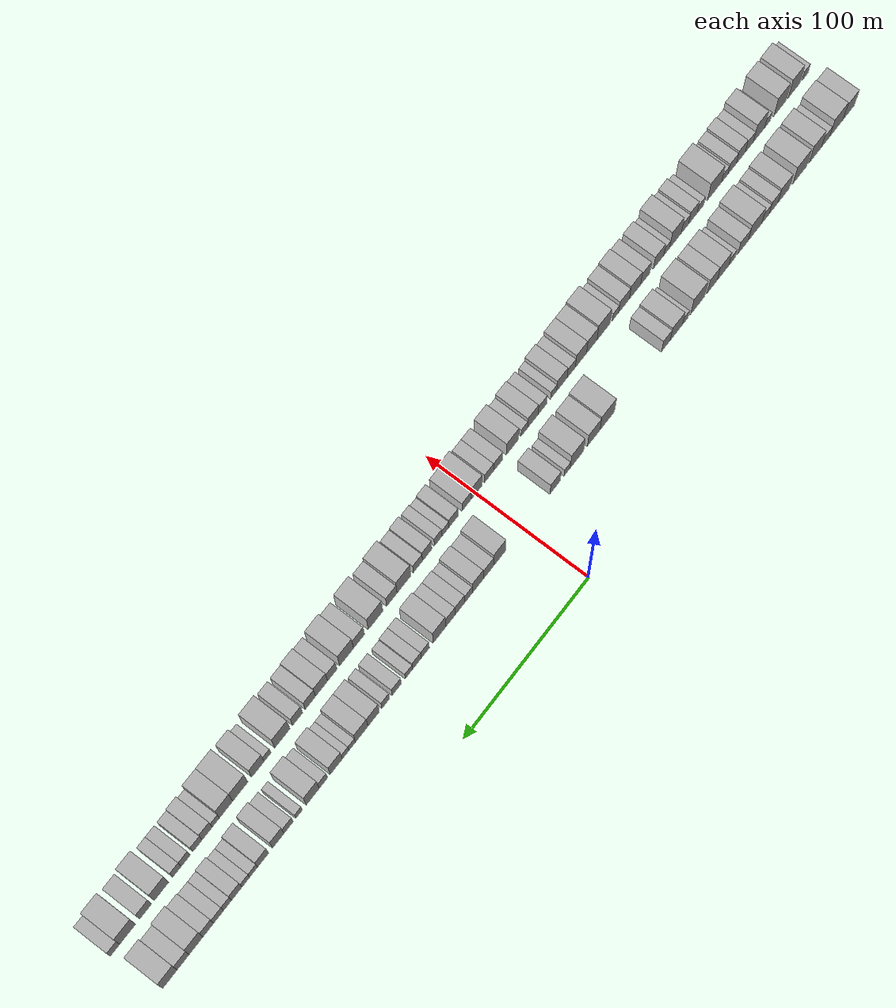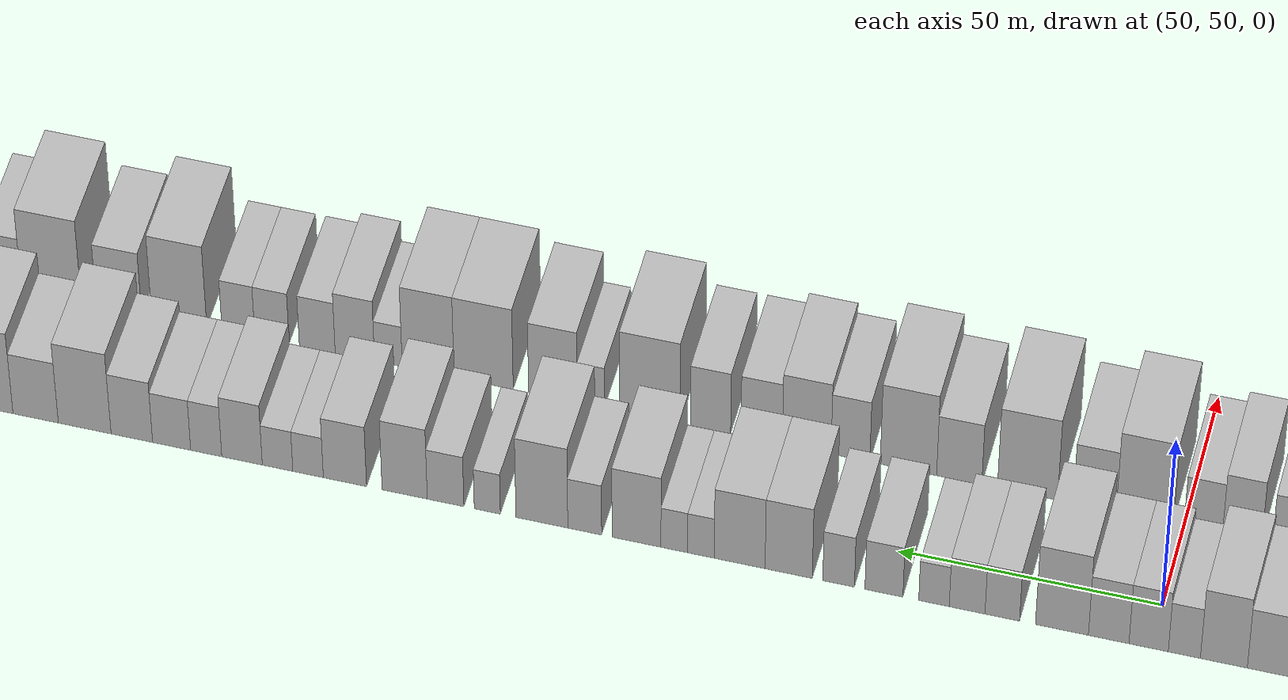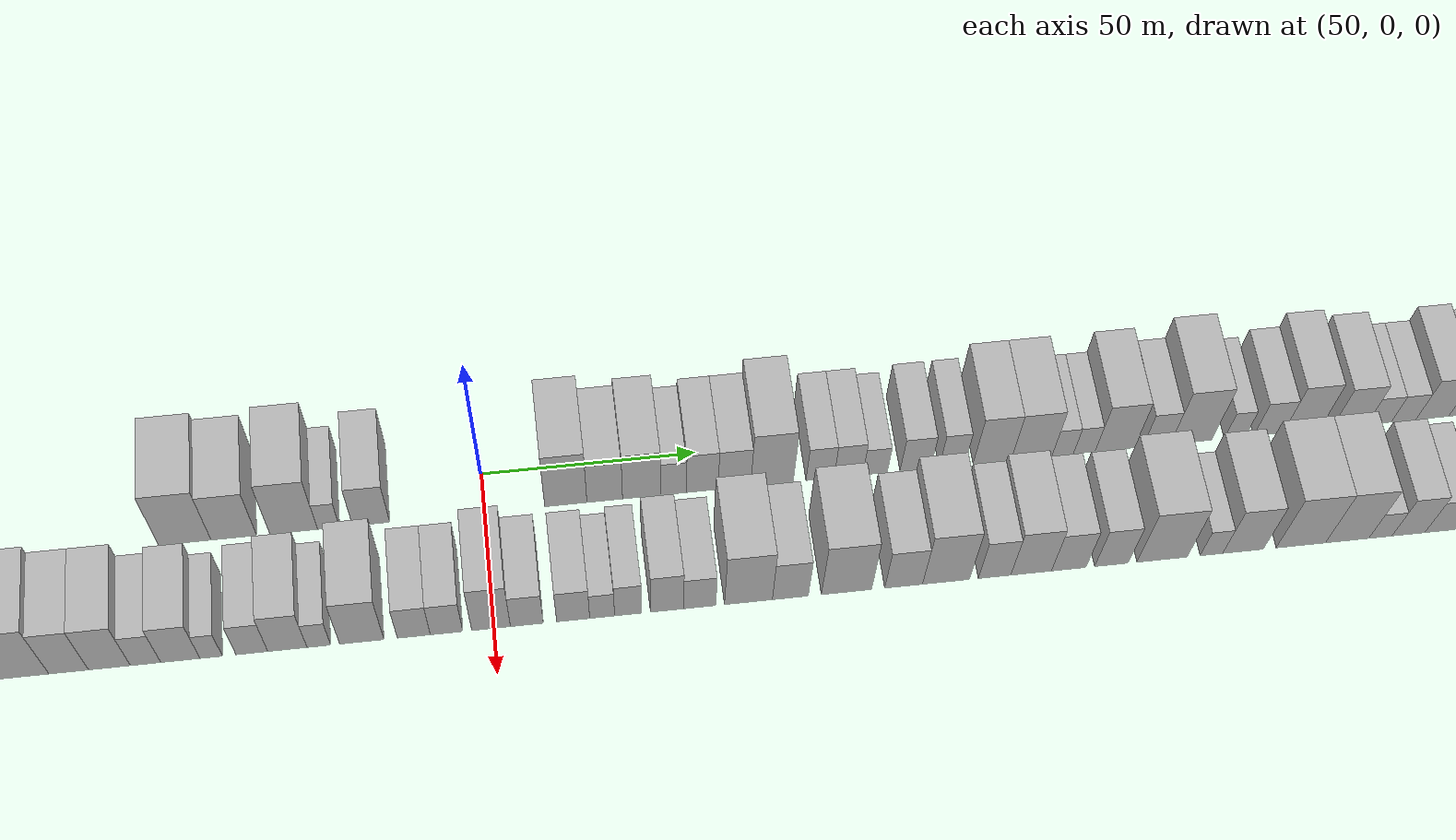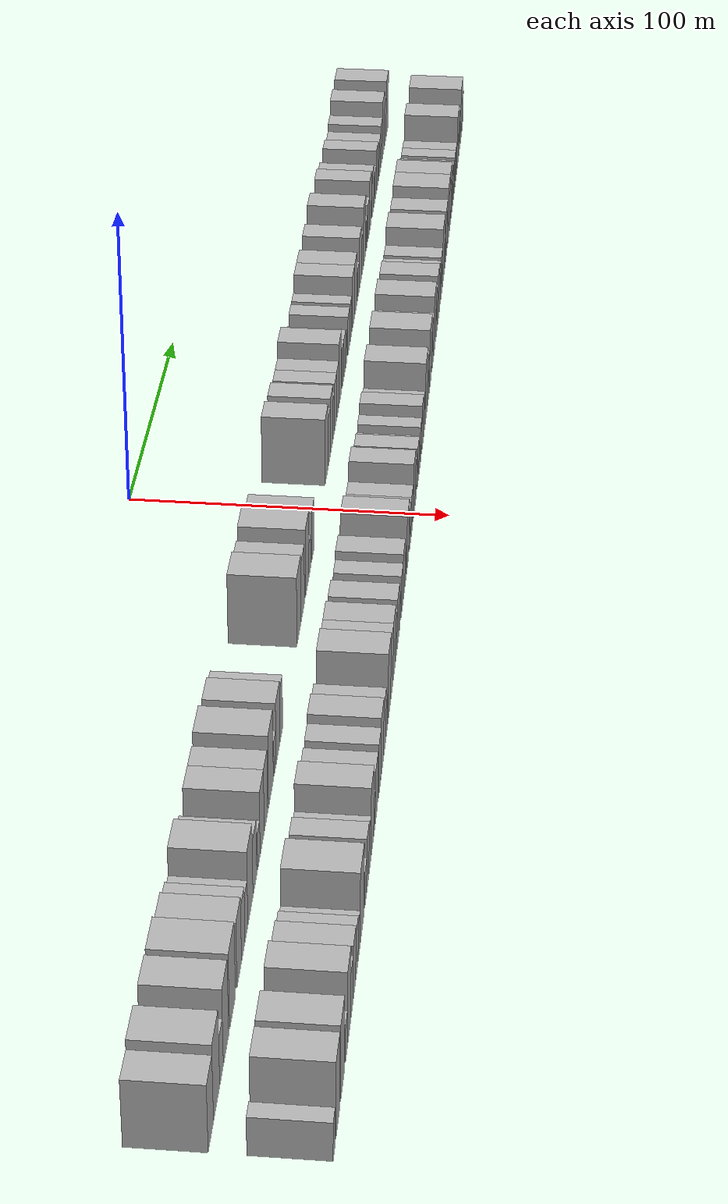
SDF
<sdf version="1.6">
 <world name="default">
  <scene>
   <sky><clouds><speed>12</speed></clouds></sky>
   <ambient>0.4 0.4 0.4 1</ambient>
   <background>0.7 0.7 0.7 1</background>
   <shadows>1</shadows>
  </scene>
  <gravity>0 0 -9.8066</gravity>
  <magnetic_field>6e-06 2.3e-05 -4.2e-05</magnetic_field>
  <physics default="0" name="default_physics" type="ode">
   <ode>
    <solver>
     <type>quick</type>
     <iters>10</iters>
     <sor>1.0</sor>
     <use_dynamic_moi_rescaling>0</use_dynamic_moi_rescaling>
    </solver>
    <constraints>
     <cfm>0</cfm>
     <erp>0.2</erp>
     <contact_max_correcting_vel>100</contact_max_correcting_vel>
     <contact_surface_layer>0.001</contact_surface_layer>
    </constraints>
   </ode>
   <max_step_size>0.004</max_step_size>
   <real_time_factor>1</real_time_factor>
   <real_time_update_rate>250</real_time_update_rate>
  </physics>
  <light name="sun" type="directional">
   <pose>0 0 10 0 0 0</pose>
   <diffuse>0.8 0.8 0.8 1</diffuse>
   <specular>0.2 0.2 0.2 1</specular>
   <attenuation>
    <range>1000</range>
    <constant>0.9</constant>
    <linear>0.01</linear>
    <quadratic>0.001</quadratic>
   </attenuation>
   <direction>-0.5 0.1 -0.9</direction>
  </light>
  <model name="building_1">
   <static>1</static>
   <pose>50.0000 -272.9973 0 0.000000 0.000000 0.000000</pose>
   <link name="link">
    <pose>0 0 10.50 0 0 0</pose>
    <collision name="collision"><geometry><box><size>20.0000 10.0054 21.0000</size></box></geometry></collision>
    <visual name="visual">
     <cast_shadows>0</cast_shadows>
     <geometry><box><size>20.0000 10.0054 21.0000</size></box></geometry>
     <material>
      <script>
       <uri>model://HANNAS_wall/materials/scripts</uri>
       <uri>model://HANNAS_wall/materials/textures</uri>
       <name>vrc/HANNAS_wall</name>
      </script>
     </material>
    </visual>
   </link>
  </model>
  <model name="building_2">
   <static>1</static>
   <pose>50.0000 -262.0783 0 0.000000 0.000000 0.000000</pose>
   <link name="link">
    <pose>0 0 12.00 0 0 0</pose>
    <collision name="collision"><geometry><box><size>20.0000 11.8327 24.0000</size></box></geometry></collision>
    <visual name="visual">
     <cast_shadows>0</cast_shadows>
     <geometry><box><size>20.0000 11.8327 24.0000</size></box></geometry>
     <material>
      <script>
       <uri>model://HANNAS_wall/materials/scripts</uri>
       <uri>model://HANNAS_wall/materials/textures</uri>
       <name>vrc/HANNAS_wall</name>
      </script>
     </material>
    </visual>
   </link>
  </model>
  <model name="building_3">
   <static>1</static>
   <pose>50.0000 -252.6162 0 0.000000 0.000000 0.000000</pose>
   <link name="link">
    <pose>0 0 7.50 0 0 0</pose>
    <collision name="collision"><geometry><box><size>20.0000 7.0915 15.0000</size></box></geometry></collision>
    <visual name="visual">
     <cast_shadows>0</cast_shadows>
     <geometry><box><size>20.0000 7.0915 15.0000</size></box></geometry>
     <material>
      <script>
       <uri>model://HANNAS_wall/materials/scripts</uri>
       <uri>model://HANNAS_wall/materials/textures</uri>
       <name>vrc/HANNAS_wall</name>
      </script>
     </material>
    </visual>
   </link>
  </model>
  <model name="building_4">
   <static>1</static>
   <pose>50.0000 -243.7639 0 0.000000 0.000000 0.000000</pose>
   <link name="link">
    <pose>0 0 12.00 0 0 0</pose>
    <collision name="collision"><geometry><box><size>20.0000 10.6131 24.0000</size></box></geometry></collision>
    <visual name="visual">
     <cast_shadows>0</cast_shadows>
     <geometry><box><size>20.0000 10.6131 24.0000</size></box></geometry>
     <material>
      <script>
       <uri>model://HANNAS_wall/materials/scripts</uri>
       <uri>model://HANNAS_wall/materials/textures</uri>
       <name>vrc/HANNAS_wall</name>
      </script>
     </material>
    </visual>
   </link>
  </model>
  <model name="building_5">
   <static>1</static>
   <pose>50.0000 -230.4985 0 0.000000 0.000000 0.000000</pose>
   <link name="link">
    <pose>0 0 12.00 0 0 0</pose>
    <collision name="collision"><geometry><box><size>20.0000 11.9177 24.0000</size></box></geometry></collision>
    <visual name="visual">
     <cast_shadows>0</cast_shadows>
     <geometry><box><size>20.0000 11.9177 24.0000</size></box></geometry>
     <material>
      <script>
       <uri>model://HANNAS_wall/materials/scripts</uri>
       <uri>model://HANNAS_wall/materials/textures</uri>
       <name>vrc/HANNAS_wall</name>
      </script>
     </material>
    </visual>
   </link>
  </model>
  <model name="building_6">
   <static>1</static>
   <pose>50.0000 -216.6666 0 0.000000 0.000000 0.000000</pose>
   <link name="link">
    <pose>0 0 10.50 0 0 0</pose>
    <collision name="collision"><geometry><box><size>20.0000 9.7462 21.0000</size></box></geometry></collision>
    <visual name="visual">
     <cast_shadows>0</cast_shadows>
     <geometry><box><size>20.0000 9.7462 21.0000</size></box></geometry>
     <material>
      <script>
       <uri>model://HANNAS_wall/materials/scripts</uri>
       <uri>model://HANNAS_wall/materials/textures</uri>
       <name>vrc/HANNAS_wall</name>
      </script>
     </material>
    </visual>
   </link>
  </model>
  <model name="building_7">
   <static>1</static>
   <pose>50.0000 -208.0286 0 0.000000 0.000000 0.000000</pose>
   <link name="link">
    <pose>0 0 9.00 0 0 0</pose>
    <collision name="collision"><geometry><box><size>20.0000 7.5296 18.0000</size></box></geometry></collision>
    <visual name="visual">
     <cast_shadows>0</cast_shadows>
     <geometry><box><size>20.0000 7.5296 18.0000</size></box></geometry>
     <material>
      <script>
       <uri>model://HANNAS_wall/materials/scripts</uri>
       <uri>model://HANNAS_wall/materials/textures</uri>
       <name>vrc/HANNAS_wall</name>
      </script>
     </material>
    </visual>
   </link>
  </model>
  <model name="building_8">
   <static>1</static>
   <pose>50.0000 -201.1453 0 0.000000 0.000000 0.000000</pose>
   <link name="link">
    <pose>0 0 7.50 0 0 0</pose>
    <collision name="collision"><geometry><box><size>20.0000 6.2371 15.0000</size></box></geometry></collision>
    <visual name="visual">
     <cast_shadows>0</cast_shadows>
     <geometry><box><size>20.0000 6.2371 15.0000</size></box></geometry>
     <material>
      <script>
       <uri>model://HANNAS_wall/materials/scripts</uri>
       <uri>model://HANNAS_wall/materials/textures</uri>
       <name>vrc/HANNAS_wall</name>
      </script>
     </material>
    </visual>
   </link>
  </model>
  <model name="building_9">
   <static>1</static>
   <pose>50.0000 -192.2525 0 0.000000 0.000000 0.000000</pose>
   <link name="link">
    <pose>0 0 12.00 0 0 0</pose>
    <collision name="collision"><geometry><box><size>20.0000 11.5486 24.0000</size></box></geometry></collision>
    <visual name="visual">
     <cast_shadows>0</cast_shadows>
     <geometry><box><size>20.0000 11.5486 24.0000</size></box></geometry>
     <material>
      <script>
       <uri>model://HANNAS_wall/materials/scripts</uri>
       <uri>model://HANNAS_wall/materials/textures</uri>
       <name>vrc/HANNAS_wall</name>
      </script>
     </material>
    </visual>
   </link>
  </model>
  <model name="building_10">
   <static>1</static>
   <pose>50.0000 -182.0756 0 0.000000 0.000000 0.000000</pose>
   <link name="link">
    <pose>0 0 9.00 0 0 0</pose>
    <collision name="collision"><geometry><box><size>20.0000 8.8052 18.0000</size></box></geometry></collision>
    <visual name="visual">
     <cast_shadows>0</cast_shadows>
     <geometry><box><size>20.0000 8.8052 18.0000</size></box></geometry>
     <material>
      <script>
       <uri>model://HANNAS_wall/materials/scripts</uri>
       <uri>model://HANNAS_wall/materials/textures</uri>
       <name>vrc/HANNAS_wall</name>
      </script>
     </material>
    </visual>
   </link>
  </model>
  <model name="building_11">
   <static>1</static>
   <pose>50.0000 -172.8159 0 0.000000 0.000000 0.000000</pose>
   <link name="link">
    <pose>0 0 6.00 0 0 0</pose>
    <collision name="collision"><geometry><box><size>20.0000 5.7141 12.0000</size></box></geometry></collision>
    <visual name="visual">
     <cast_shadows>0</cast_shadows>
     <geometry><box><size>20.0000 5.7141 12.0000</size></box></geometry>
     <material>
      <script>
       <uri>model://HANNAS_wall/materials/scripts</uri>
       <uri>model://HANNAS_wall/materials/textures</uri>
       <name>vrc/HANNAS_wall</name>
      </script>
     </material>
    </visual>
   </link>
  </model>
  <model name="building_12">
   <static>1</static>
   <pose>50.0000 -165.0856 0 0.000000 0.000000 0.000000</pose>
   <link name="link">
    <pose>0 0 10.50 0 0 0</pose>
    <collision name="collision"><geometry><box><size>20.0000 9.7466 21.0000</size></box></geometry></collision>
    <visual name="visual">
     <cast_shadows>0</cast_shadows>
     <geometry><box><size>20.0000 9.7466 21.0000</size></box></geometry>
     <material>
      <script>
       <uri>model://HANNAS_wall/materials/scripts</uri>
       <uri>model://HANNAS_wall/materials/textures</uri>
       <name>vrc/HANNAS_wall</name>
      </script>
     </material>
    </visual>
   </link>
  </model>
  <model name="building_13">
   <static>1</static>
   <pose>50.0000 -156.0007 0 0.000000 0.000000 0.000000</pose>
   <link name="link">
    <pose>0 0 10.50 0 0 0</pose>
    <collision name="collision"><geometry><box><size>20.0000 8.4233 21.0000</size></box></geometry></collision>
    <visual name="visual">
     <cast_shadows>0</cast_shadows>
     <geometry><box><size>20.0000 8.4233 21.0000</size></box></geometry>
     <material>
      <script>
       <uri>model://HANNAS_wall/materials/scripts</uri>
       <uri>model://HANNAS_wall/materials/textures</uri>
       <name>vrc/HANNAS_wall</name>
      </script>
     </material>
    </visual>
   </link>
  </model>
  <model name="building_14">
   <static>1</static>
   <pose>50.0000 -143.8482 0 0.000000 0.000000 0.000000</pose>
   <link name="link">
    <pose>0 0 12.00 0 0 0</pose>
    <collision name="collision"><geometry><box><size>20.0000 11.8817 24.0000</size></box></geometry></collision>
    <visual name="visual">
     <cast_shadows>0</cast_shadows>
     <geometry><box><size>20.0000 11.8817 24.0000</size></box></geometry>
     <material>
      <script>
       <uri>model://HANNAS_wall/materials/scripts</uri>
       <uri>model://HANNAS_wall/materials/textures</uri>
       <name>vrc/HANNAS_wall</name>
      </script>
     </material>
    </visual>
   </link>
  </model>
  <model name="building_15">
   <static>1</static>
   <pose>50.0000 -133.4855 0 0.000000 0.000000 0.000000</pose>
   <link name="link">
    <pose>0 0 6.00 0 0 0</pose>
    <collision name="collision"><geometry><box><size>20.0000 4.8438 12.0000</size></box></geometry></collision>
    <visual name="visual">
     <cast_shadows>0</cast_shadows>
     <geometry><box><size>20.0000 4.8438 12.0000</size></box></geometry>
     <material>
      <script>
       <uri>model://HANNAS_wall/materials/scripts</uri>
       <uri>model://HANNAS_wall/materials/textures</uri>
       <name>vrc/HANNAS_wall</name>
      </script>
     </material>
    </visual>
   </link>
  </model>
  <model name="building_16">
   <static>1</static>
   <pose>50.0000 -125.9108 0 0.000000 0.000000 0.000000</pose>
   <link name="link">
    <pose>0 0 10.50 0 0 0</pose>
    <collision name="collision"><geometry><box><size>20.0000 10.3055 21.0000</size></box></geometry></collision>
    <visual name="visual">
     <cast_shadows>0</cast_shadows>
     <geometry><box><size>20.0000 10.3055 21.0000</size></box></geometry>
     <material>
      <script>
       <uri>model://HANNAS_wall/materials/scripts</uri>
       <uri>model://HANNAS_wall/materials/textures</uri>
       <name>vrc/HANNAS_wall</name>
      </script>
     </material>
    </visual>
   </link>
  </model>
  <model name="building_17">
   <static>1</static>
   <pose>50.0000 -117.1440 0 0.000000 0.000000 0.000000</pose>
   <link name="link">
    <pose>0 0 9.00 0 0 0</pose>
    <collision name="collision"><geometry><box><size>20.0000 7.2282 18.0000</size></box></geometry></collision>
    <visual name="visual">
     <cast_shadows>0</cast_shadows>
     <geometry><box><size>20.0000 7.2282 18.0000</size></box></geometry>
     <material>
      <script>
       <uri>model://HANNAS_wall/materials/scripts</uri>
       <uri>model://HANNAS_wall/materials/textures</uri>
       <name>vrc/HANNAS_wall</name>
      </script>
     </material>
    </visual>
   </link>
  </model>
  <model name="building_18">
   <static>1</static>
   <pose>50.0000 -68.6288 0 0.000000 0.000000 0.000000</pose>
   <link name="link">
    <pose>0 0 12.00 0 0 0</pose>
    <collision name="collision"><geometry><box><size>20.0000 11.9341 24.0000</size></box></geometry></collision>
    <visual name="visual">
     <cast_shadows>0</cast_shadows>
     <geometry><box><size>20.0000 11.9341 24.0000</size></box></geometry>
     <material>
      <script>
       <uri>model://HANNAS_wall/materials/scripts</uri>
       <uri>model://HANNAS_wall/materials/textures</uri>
       <name>vrc/HANNAS_wall</name>
      </script>
     </material>
    </visual>
   </link>
  </model>
  <model name="building_19">
   <static>1</static>
   <pose>50.0000 -57.4570 0 0.000000 0.000000 0.000000</pose>
   <link name="link">
    <pose>0 0 10.50 0 0 0</pose>
    <collision name="collision"><geometry><box><size>20.0000 10.4093 21.0000</size></box></geometry></collision>
    <visual name="visual">
     <cast_shadows>0</cast_shadows>
     <geometry><box><size>20.0000 10.4093 21.0000</size></box></geometry>
     <material>
      <script>
       <uri>model://HANNAS_wall/materials/scripts</uri>
       <uri>model://HANNAS_wall/materials/textures</uri>
       <name>vrc/HANNAS_wall</name>
      </script>
     </material>
    </visual>
   </link>
  </model>
  <model name="building_20">
   <static>1</static>
   <pose>50.0000 -43.7756 0 0.000000 0.000000 0.000000</pose>
   <link name="link">
    <pose>0 0 12.00 0 0 0</pose>
    <collision name="collision"><geometry><box><size>20.0000 10.9534 24.0000</size></box></geometry></collision>
    <visual name="visual">
     <cast_shadows>0</cast_shadows>
     <geometry><box><size>20.0000 10.9534 24.0000</size></box></geometry>
     <material>
      <script>
       <uri>model://HANNAS_wall/materials/scripts</uri>
       <uri>model://HANNAS_wall/materials/textures</uri>
       <name>vrc/HANNAS_wall</name>
      </script>
     </material>
    </visual>
   </link>
  </model>
  <model name="building_21">
   <static>1</static>
   <pose>50.0000 -35.7943 0 0.000000 0.000000 0.000000</pose>
   <link name="link">
    <pose>0 0 6.00 0 0 0</pose>
    <collision name="collision"><geometry><box><size>20.0000 5.0093 12.0000</size></box></geometry></collision>
    <visual name="visual">
     <cast_shadows>0</cast_shadows>
     <geometry><box><size>20.0000 5.0093 12.0000</size></box></geometry>
     <material>
      <script>
       <uri>model://HANNAS_wall/materials/scripts</uri>
       <uri>model://HANNAS_wall/materials/textures</uri>
       <name>vrc/HANNAS_wall</name>
      </script>
     </material>
    </visual>
   </link>
  </model>
  <model name="building_22">
   <static>1</static>
   <pose>50.0000 -26.0420 0 0.000000 0.000000 0.000000</pose>
   <link name="link">
    <pose>0 0 9.00 0 0 0</pose>
    <collision name="collision"><geometry><box><size>20.0000 8.4953 18.0000</size></box></geometry></collision>
    <visual name="visual">
     <cast_shadows>0</cast_shadows>
     <geometry><box><size>20.0000 8.4953 18.0000</size></box></geometry>
     <material>
      <script>
       <uri>model://HANNAS_wall/materials/scripts</uri>
       <uri>model://HANNAS_wall/materials/textures</uri>
       <name>vrc/HANNAS_wall</name>
      </script>
     </material>
    </visual>
   </link>
  </model>
  <model name="building_23">
   <static>1</static>
   <pose>50.0000 18.8368 0 0.000000 0.000000 0.000000</pose>
   <link name="link">
    <pose>0 0 12.00 0 0 0</pose>
    <collision name="collision"><geometry><box><size>20.0000 9.7541 24.0000</size></box></geometry></collision>
    <visual name="visual">
     <cast_shadows>0</cast_shadows>
     <geometry><box><size>20.0000 9.7541 24.0000</size></box></geometry>
     <material>
      <script>
       <uri>model://HANNAS_wall/materials/scripts</uri>
       <uri>model://HANNAS_wall/materials/textures</uri>
       <name>vrc/HANNAS_wall</name>
      </script>
     </material>
    </visual>
   </link>
  </model>
  <model name="building_24">
   <static>1</static>
   <pose>50.0000 27.8491 0 0.000000 0.000000 0.000000</pose>
   <link name="link">
    <pose>0 0 9.00 0 0 0</pose>
    <collision name="collision"><geometry><box><size>20.0000 8.2705 18.0000</size></box></geometry></collision>
    <visual name="visual">
     <cast_shadows>0</cast_shadows>
     <geometry><box><size>20.0000 8.2705 18.0000</size></box></geometry>
     <material>
      <script>
       <uri>model://HANNAS_wall/materials/scripts</uri>
       <uri>model://HANNAS_wall/materials/textures</uri>
       <name>vrc/HANNAS_wall</name>
      </script>
     </material>
    </visual>
   </link>
  </model>
  <model name="building_25">
   <static>1</static>
   <pose>50.0000 36.3773 0 0.000000 0.000000 0.000000</pose>
   <link name="link">
    <pose>0 0 10.50 0 0 0</pose>
    <collision name="collision"><geometry><box><size>20.0000 8.7859 21.0000</size></box></geometry></collision>
    <visual name="visual">
     <cast_shadows>0</cast_shadows>
     <geometry><box><size>20.0000 8.7859 21.0000</size></box></geometry>
     <material>
      <script>
       <uri>model://HANNAS_wall/materials/scripts</uri>
       <uri>model://HANNAS_wall/materials/textures</uri>
       <name>vrc/HANNAS_wall</name>
      </script>
     </material>
    </visual>
   </link>
  </model>
  <model name="building_26">
   <static>1</static>
   <pose>50.0000 43.7820 0 0.000000 0.000000 0.000000</pose>
   <link name="link">
    <pose>0 0 7.50 0 0 0</pose>
    <collision name="collision"><geometry><box><size>20.0000 6.0235 15.0000</size></box></geometry></collision>
    <visual name="visual">
     <cast_shadows>0</cast_shadows>
     <geometry><box><size>20.0000 6.0235 15.0000</size></box></geometry>
     <material>
      <script>
       <uri>model://HANNAS_wall/materials/scripts</uri>
       <uri>model://HANNAS_wall/materials/textures</uri>
       <name>vrc/HANNAS_wall</name>
      </script>
     </material>
    </visual>
   </link>
  </model>
  <model name="building_27">
   <static>1</static>
   <pose>50.0000 50.4874 0 0.000000 0.000000 0.000000</pose>
   <link name="link">
    <pose>0 0 9.00 0 0 0</pose>
    <collision name="collision"><geometry><box><size>20.0000 7.3873 18.0000</size></box></geometry></collision>
    <visual name="visual">
     <cast_shadows>0</cast_shadows>
     <geometry><box><size>20.0000 7.3873 18.0000</size></box></geometry>
     <material>
      <script>
       <uri>model://HANNAS_wall/materials/scripts</uri>
       <uri>model://HANNAS_wall/materials/textures</uri>
       <name>vrc/HANNAS_wall</name>
      </script>
     </material>
    </visual>
   </link>
  </model>
  <model name="building_28">
   <static>1</static>
   <pose>50.0000 57.9974 0 0.000000 0.000000 0.000000</pose>
   <link name="link">
    <pose>0 0 9.00 0 0 0</pose>
    <collision name="collision"><geometry><box><size>20.0000 7.6327 18.0000</size></box></geometry></collision>
    <visual name="visual">
     <cast_shadows>0</cast_shadows>
     <geometry><box><size>20.0000 7.6327 18.0000</size></box></geometry>
     <material>
      <script>
       <uri>model://HANNAS_wall/materials/scripts</uri>
       <uri>model://HANNAS_wall/materials/textures</uri>
       <name>vrc/HANNAS_wall</name>
      </script>
     </material>
    </visual>
   </link>
  </model>
  <model name="building_29">
   <static>1</static>
   <pose>50.0000 66.8015 0 0.000000 0.000000 0.000000</pose>
   <link name="link">
    <pose>0 0 12.00 0 0 0</pose>
    <collision name="collision"><geometry><box><size>20.0000 9.9755 24.0000</size></box></geometry></collision>
    <visual name="visual">
     <cast_shadows>0</cast_shadows>
     <geometry><box><size>20.0000 9.9755 24.0000</size></box></geometry>
     <material>
      <script>
       <uri>model://HANNAS_wall/materials/scripts</uri>
       <uri>model://HANNAS_wall/materials/textures</uri>
       <name>vrc/HANNAS_wall</name>
      </script>
     </material>
    </visual>
   </link>
  </model>
  <model name="building_30">
   <static>1</static>
   <pose>50.0000 78.0534 0 0.000000 0.000000 0.000000</pose>
   <link name="link">
    <pose>0 0 7.50 0 0 0</pose>
    <collision name="collision"><geometry><box><size>20.0000 6.5283 15.0000</size></box></geometry></collision>
    <visual name="visual">
     <cast_shadows>0</cast_shadows>
     <geometry><box><size>20.0000 6.5283 15.0000</size></box></geometry>
     <material>
      <script>
       <uri>model://HANNAS_wall/materials/scripts</uri>
       <uri>model://HANNAS_wall/materials/textures</uri>
       <name>vrc/HANNAS_wall</name>
      </script>
     </material>
    </visual>
   </link>
  </model>
  <model name="building_31">
   <static>1</static>
   <pose>50.0000 84.7035 0 0.000000 0.000000 0.000000</pose>
   <link name="link">
    <pose>0 0 7.50 0 0 0</pose>
    <collision name="collision"><geometry><box><size>20.0000 6.7718 15.0000</size></box></geometry></collision>
    <visual name="visual">
     <cast_shadows>0</cast_shadows>
     <geometry><box><size>20.0000 6.7718 15.0000</size></box></geometry>
     <material>
      <script>
       <uri>model://HANNAS_wall/materials/scripts</uri>
       <uri>model://HANNAS_wall/materials/textures</uri>
       <name>vrc/HANNAS_wall</name>
      </script>
     </material>
    </visual>
   </link>
  </model>
  <model name="building_32">
   <static>1</static>
   <pose>50.0000 90.9740 0 0.000000 0.000000 0.000000</pose>
   <link name="link">
    <pose>0 0 6.00 0 0 0</pose>
    <collision name="collision"><geometry><box><size>20.0000 5.7691 12.0000</size></box></geometry></collision>
    <visual name="visual">
     <cast_shadows>0</cast_shadows>
     <geometry><box><size>20.0000 5.7691 12.0000</size></box></geometry>
     <material>
      <script>
       <uri>model://HANNAS_wall/materials/scripts</uri>
       <uri>model://HANNAS_wall/materials/textures</uri>
       <name>vrc/HANNAS_wall</name>
      </script>
     </material>
    </visual>
   </link>
  </model>
  <model name="building_33">
   <static>1</static>
   <pose>50.0000 100.4630 0 0.000000 0.000000 0.000000</pose>
   <link name="link">
    <pose>0 0 7.50 0 0 0</pose>
    <collision name="collision"><geometry><box><size>20.0000 7.2090 15.0000</size></box></geometry></collision>
    <visual name="visual">
     <cast_shadows>0</cast_shadows>
     <geometry><box><size>20.0000 7.2090 15.0000</size></box></geometry>
     <material>
      <script>
       <uri>model://HANNAS_wall/materials/scripts</uri>
       <uri>model://HANNAS_wall/materials/textures</uri>
       <name>vrc/HANNAS_wall</name>
      </script>
     </material>
    </visual>
   </link>
  </model>
  <model name="building_34">
   <static>1</static>
   <pose>50.0000 109.0796 0 0.000000 0.000000 0.000000</pose>
   <link name="link">
    <pose>0 0 7.50 0 0 0</pose>
    <collision name="collision"><geometry><box><size>20.0000 6.0240 15.0000</size></box></geometry></collision>
    <visual name="visual">
     <cast_shadows>0</cast_shadows>
     <geometry><box><size>20.0000 6.0240 15.0000</size></box></geometry>
     <material>
      <script>
       <uri>model://HANNAS_wall/materials/scripts</uri>
       <uri>model://HANNAS_wall/materials/textures</uri>
       <name>vrc/HANNAS_wall</name>
      </script>
     </material>
    </visual>
   </link>
  </model>
  <model name="building_35">
   <static>1</static>
   <pose>50.0000 118.5853 0 0.000000 0.000000 0.000000</pose>
   <link name="link">
    <pose>0 0 10.50 0 0 0</pose>
    <collision name="collision"><geometry><box><size>20.0000 8.9874 21.0000</size></box></geometry></collision>
    <visual name="visual">
     <cast_shadows>0</cast_shadows>
     <geometry><box><size>20.0000 8.9874 21.0000</size></box></geometry>
     <material>
      <script>
       <uri>model://HANNAS_wall/materials/scripts</uri>
       <uri>model://HANNAS_wall/materials/textures</uri>
       <name>vrc/HANNAS_wall</name>
      </script>
     </material>
    </visual>
   </link>
  </model>
  <model name="building_36">
   <static>1</static>
   <pose>50.0000 127.9263 0 0.000000 0.000000 0.000000</pose>
   <link name="link">
    <pose>0 0 10.50 0 0 0</pose>
    <collision name="collision"><geometry><box><size>20.0000 9.6948 21.0000</size></box></geometry></collision>
    <visual name="visual">
     <cast_shadows>0</cast_shadows>
     <geometry><box><size>20.0000 9.6948 21.0000</size></box></geometry>
     <material>
      <script>
       <uri>model://HANNAS_wall/materials/scripts</uri>
       <uri>model://HANNAS_wall/materials/textures</uri>
       <name>vrc/HANNAS_wall</name>
      </script>
     </material>
    </visual>
   </link>
  </model>
  <model name="building_37">
   <static>1</static>
   <pose>50.0000 135.3157 0 0.000000 0.000000 0.000000</pose>
   <link name="link">
    <pose>0 0 6.00 0 0 0</pose>
    <collision name="collision"><geometry><box><size>20.0000 5.0840 12.0000</size></box></geometry></collision>
    <visual name="visual">
     <cast_shadows>0</cast_shadows>
     <geometry><box><size>20.0000 5.0840 12.0000</size></box></geometry>
     <material>
      <script>
       <uri>model://HANNAS_wall/materials/scripts</uri>
       <uri>model://HANNAS_wall/materials/textures</uri>
       <name>vrc/HANNAS_wall</name>
      </script>
     </material>
    </visual>
   </link>
  </model>
  <model name="building_38">
   <static>1</static>
   <pose>50.0000 140.4086 0 0.000000 0.000000 0.000000</pose>
   <link name="link">
    <pose>0 0 6.00 0 0 0</pose>
    <collision name="collision"><geometry><box><size>20.0000 5.1019 12.0000</size></box></geometry></collision>
    <visual name="visual">
     <cast_shadows>0</cast_shadows>
     <geometry><box><size>20.0000 5.1019 12.0000</size></box></geometry>
     <material>
      <script>
       <uri>model://HANNAS_wall/materials/scripts</uri>
       <uri>model://HANNAS_wall/materials/textures</uri>
       <name>vrc/HANNAS_wall</name>
      </script>
     </material>
    </visual>
   </link>
  </model>
  <model name="building_39">
   <static>1</static>
   <pose>50.0000 147.6372 0 0.000000 0.000000 0.000000</pose>
   <link name="link">
    <pose>0 0 10.50 0 0 0</pose>
    <collision name="collision"><geometry><box><size>20.0000 9.3553 21.0000</size></box></geometry></collision>
    <visual name="visual">
     <cast_shadows>0</cast_shadows>
     <geometry><box><size>20.0000 9.3553 21.0000</size></box></geometry>
     <material>
      <script>
       <uri>model://HANNAS_wall/materials/scripts</uri>
       <uri>model://HANNAS_wall/materials/textures</uri>
       <name>vrc/HANNAS_wall</name>
      </script>
     </material>
    </visual>
   </link>
  </model>
  <model name="building_40">
   <static>1</static>
   <pose>50.0000 157.5673 0 0.000000 0.000000 0.000000</pose>
   <link name="link">
    <pose>0 0 7.50 0 0 0</pose>
    <collision name="collision"><geometry><box><size>20.0000 6.5049 15.0000</size></box></geometry></collision>
    <visual name="visual">
     <cast_shadows>0</cast_shadows>
     <geometry><box><size>20.0000 6.5049 15.0000</size></box></geometry>
     <material>
      <script>
       <uri>model://HANNAS_wall/materials/scripts</uri>
       <uri>model://HANNAS_wall/materials/textures</uri>
       <name>vrc/HANNAS_wall</name>
      </script>
     </material>
    </visual>
   </link>
  </model>
  <model name="building_41">
   <static>1</static>
   <pose>50.0000 165.8030 0 0.000000 0.000000 0.000000</pose>
   <link name="link">
    <pose>0 0 12.00 0 0 0</pose>
    <collision name="collision"><geometry><box><size>20.0000 9.9665 24.0000</size></box></geometry></collision>
    <visual name="visual">
     <cast_shadows>0</cast_shadows>
     <geometry><box><size>20.0000 9.9665 24.0000</size></box></geometry>
     <material>
      <script>
       <uri>model://HANNAS_wall/materials/scripts</uri>
       <uri>model://HANNAS_wall/materials/textures</uri>
       <name>vrc/HANNAS_wall</name>
      </script>
     </material>
    </visual>
   </link>
  </model>
  <model name="building_42">
   <static>1</static>
   <pose>50.0000 176.2996 0 0.000000 0.000000 0.000000</pose>
   <link name="link">
    <pose>0 0 6.00 0 0 0</pose>
    <collision name="collision"><geometry><box><size>20.0000 5.0267 12.0000</size></box></geometry></collision>
    <visual name="visual">
     <cast_shadows>0</cast_shadows>
     <geometry><box><size>20.0000 5.0267 12.0000</size></box></geometry>
     <material>
      <script>
       <uri>model://HANNAS_wall/materials/scripts</uri>
       <uri>model://HANNAS_wall/materials/textures</uri>
       <name>vrc/HANNAS_wall</name>
      </script>
     </material>
    </visual>
   </link>
  </model>
  <model name="building_43">
   <static>1</static>
   <pose>50.0000 184.3478 0 0.000000 0.000000 0.000000</pose>
   <link name="link">
    <pose>0 0 7.50 0 0 0</pose>
    <collision name="collision"><geometry><box><size>20.0000 7.0698 15.0000</size></box></geometry></collision>
    <visual name="visual">
     <cast_shadows>0</cast_shadows>
     <geometry><box><size>20.0000 7.0698 15.0000</size></box></geometry>
     <material>
      <script>
       <uri>model://HANNAS_wall/materials/scripts</uri>
       <uri>model://HANNAS_wall/materials/textures</uri>
       <name>vrc/HANNAS_wall</name>
      </script>
     </material>
    </visual>
   </link>
  </model>
  <model name="building_44">
   <static>1</static>
   <pose>50.0000 192.2530 0 0.000000 0.000000 0.000000</pose>
   <link name="link">
    <pose>0 0 10.50 0 0 0</pose>
    <collision name="collision"><geometry><box><size>20.0000 8.7406 21.0000</size></box></geometry></collision>
    <visual name="visual">
     <cast_shadows>0</cast_shadows>
     <geometry><box><size>20.0000 8.7406 21.0000</size></box></geometry>
     <material>
      <script>
       <uri>model://HANNAS_wall/materials/scripts</uri>
       <uri>model://HANNAS_wall/materials/textures</uri>
       <name>vrc/HANNAS_wall</name>
      </script>
     </material>
    </visual>
   </link>
  </model>
  <model name="building_45">
   <static>1</static>
   <pose>50.0000 203.8163 0 0.000000 0.000000 0.000000</pose>
   <link name="link">
    <pose>0 0 9.00 0 0 0</pose>
    <collision name="collision"><geometry><box><size>20.0000 8.3859 18.0000</size></box></geometry></collision>
    <visual name="visual">
     <cast_shadows>0</cast_shadows>
     <geometry><box><size>20.0000 8.3859 18.0000</size></box></geometry>
     <material>
      <script>
       <uri>model://HANNAS_wall/materials/scripts</uri>
       <uri>model://HANNAS_wall/materials/textures</uri>
       <name>vrc/HANNAS_wall</name>
      </script>
     </material>
    </visual>
   </link>
  </model>
  <model name="building_46">
   <static>1</static>
   <pose>50.0000 210.9679 0 0.000000 0.000000 0.000000</pose>
   <link name="link">
    <pose>0 0 6.00 0 0 0</pose>
    <collision name="collision"><geometry><box><size>20.0000 5.9173 12.0000</size></box></geometry></collision>
    <visual name="visual">
     <cast_shadows>0</cast_shadows>
     <geometry><box><size>20.0000 5.9173 12.0000</size></box></geometry>
     <material>
      <script>
       <uri>model://HANNAS_wall/materials/scripts</uri>
       <uri>model://HANNAS_wall/materials/textures</uri>
       <name>vrc/HANNAS_wall</name>
      </script>
     </material>
    </visual>
   </link>
  </model>
  <model name="building_47">
   <static>1</static>
   <pose>50.0000 216.8930 0 0.000000 0.000000 0.000000</pose>
   <link name="link">
    <pose>0 0 6.00 0 0 0</pose>
    <collision name="collision"><geometry><box><size>20.0000 5.9330 12.0000</size></box></geometry></collision>
    <visual name="visual">
     <cast_shadows>0</cast_shadows>
     <geometry><box><size>20.0000 5.9330 12.0000</size></box></geometry>
     <material>
      <script>
       <uri>model://HANNAS_wall/materials/scripts</uri>
       <uri>model://HANNAS_wall/materials/textures</uri>
       <name>vrc/HANNAS_wall</name>
      </script>
     </material>
    </visual>
   </link>
  </model>
  <model name="building_48">
   <static>1</static>
   <pose>50.0000 223.8020 0 0.000000 0.000000 0.000000</pose>
   <link name="link">
    <pose>0 0 9.00 0 0 0</pose>
    <collision name="collision"><geometry><box><size>20.0000 7.8851 18.0000</size></box></geometry></collision>
    <visual name="visual">
     <cast_shadows>0</cast_shadows>
     <geometry><box><size>20.0000 7.8851 18.0000</size></box></geometry>
     <material>
      <script>
       <uri>model://HANNAS_wall/materials/scripts</uri>
       <uri>model://HANNAS_wall/materials/textures</uri>
       <name>vrc/HANNAS_wall</name>
      </script>
     </material>
    </visual>
   </link>
  </model>
  <model name="building_49">
   <static>1</static>
   <pose>50.0000 230.7724 0 0.000000 0.000000 0.000000</pose>
   <link name="link">
    <pose>0 0 7.50 0 0 0</pose>
    <collision name="collision"><geometry><box><size>20.0000 6.0558 15.0000</size></box></geometry></collision>
    <visual name="visual">
     <cast_shadows>0</cast_shadows>
     <geometry><box><size>20.0000 6.0558 15.0000</size></box></geometry>
     <material>
      <script>
       <uri>model://HANNAS_wall/materials/scripts</uri>
       <uri>model://HANNAS_wall/materials/textures</uri>
       <name>vrc/HANNAS_wall</name>
      </script>
     </material>
    </visual>
   </link>
  </model>
  <model name="building_50">
   <static>1</static>
   <pose>50.0000 237.5136 0 0.000000 0.000000 0.000000</pose>
   <link name="link">
    <pose>0 0 7.50 0 0 0</pose>
    <collision name="collision"><geometry><box><size>20.0000 7.4265 15.0000</size></box></geometry></collision>
    <visual name="visual">
     <cast_shadows>0</cast_shadows>
     <geometry><box><size>20.0000 7.4265 15.0000</size></box></geometry>
     <material>
      <script>
       <uri>model://HANNAS_wall/materials/scripts</uri>
       <uri>model://HANNAS_wall/materials/textures</uri>
       <name>vrc/HANNAS_wall</name>
      </script>
     </material>
    </visual>
   </link>
  </model>
  <model name="building_51">
   <static>1</static>
   <pose>50.0000 245.2830 0 0.000000 0.000000 0.000000</pose>
   <link name="link">
    <pose>0 0 9.00 0 0 0</pose>
    <collision name="collision"><geometry><box><size>20.0000 8.1123 18.0000</size></box></geometry></collision>
    <visual name="visual">
     <cast_shadows>0</cast_shadows>
     <geometry><box><size>20.0000 8.1123 18.0000</size></box></geometry>
     <material>
      <script>
       <uri>model://HANNAS_wall/materials/scripts</uri>
       <uri>model://HANNAS_wall/materials/textures</uri>
       <name>vrc/HANNAS_wall</name>
      </script>
     </material>
    </visual>
   </link>
  </model>
  <model name="building_52">
   <static>1</static>
   <pose>50.0000 254.5072 0 0.000000 0.000000 0.000000</pose>
   <link name="link">
    <pose>0 0 12.00 0 0 0</pose>
    <collision name="collision"><geometry><box><size>20.0000 10.3362 24.0000</size></box></geometry></collision>
    <visual name="visual">
     <cast_shadows>0</cast_shadows>
     <geometry><box><size>20.0000 10.3362 24.0000</size></box></geometry>
     <material>
      <script>
       <uri>model://HANNAS_wall/materials/scripts</uri>
       <uri>model://HANNAS_wall/materials/textures</uri>
       <name>vrc/HANNAS_wall</name>
      </script>
     </material>
    </visual>
   </link>
  </model>
  <model name="building_53">
   <static>1</static>
   <pose>50.0000 264.1224 0 0.000000 0.000000 0.000000</pose>
   <link name="link">
    <pose>0 0 9.00 0 0 0</pose>
    <collision name="collision"><geometry><box><size>20.0000 8.8940 18.0000</size></box></geometry></collision>
    <visual name="visual">
     <cast_shadows>0</cast_shadows>
     <geometry><box><size>20.0000 8.8940 18.0000</size></box></geometry>
     <material>
      <script>
       <uri>model://HANNAS_wall/materials/scripts</uri>
       <uri>model://HANNAS_wall/materials/textures</uri>
       <name>vrc/HANNAS_wall</name>
      </script>
     </material>
    </visual>
   </link>
  </model>
  <model name="building_54">
   <static>1</static>
   <pose>50.0000 273.9861 0 0.000000 0.000000 0.000000</pose>
   <link name="link">
    <pose>0 0 12.00 0 0 0</pose>
    <collision name="collision"><geometry><box><size>20.0000 10.8333 24.0000</size></box></geometry></collision>
    <visual name="visual">
     <cast_shadows>0</cast_shadows>
     <geometry><box><size>20.0000 10.8333 24.0000</size></box></geometry>
     <material>
      <script>
       <uri>model://HANNAS_wall/materials/scripts</uri>
       <uri>model://HANNAS_wall/materials/textures</uri>
       <name>vrc/HANNAS_wall</name>
      </script>
     </material>
    </visual>
   </link>
  </model>
  <model name="building_55">
   <static>1</static>
   <pose>79.0000 -275.4391 0 0.000000 0.000000 0.000000</pose>
   <link name="link">
    <pose>0 0 6.00 0 0 0</pose>
    <collision name="collision"><geometry><box><size>20.0000 5.1218 12.0000</size></box></geometry></collision>
    <visual name="visual">
     <cast_shadows>0</cast_shadows>
     <geometry><box><size>20.0000 5.1218 12.0000</size></box></geometry>
     <material>
      <script>
       <uri>model://HANNAS_wall/materials/scripts</uri>
       <uri>model://HANNAS_wall/materials/textures</uri>
       <name>vrc/HANNAS_wall</name>
      </script>
     </material>
    </visual>
   </link>
  </model>
  <model name="building_56">
   <static>1</static>
   <pose>79.0000 -265.8106 0 0.000000 0.000000 0.000000</pose>
   <link name="link">
    <pose>0 0 12.00 0 0 0</pose>
    <collision name="collision"><geometry><box><size>20.0000 10.1352 24.0000</size></box></geometry></collision>
    <visual name="visual">
     <cast_shadows>0</cast_shadows>
     <geometry><box><size>20.0000 10.1352 24.0000</size></box></geometry>
     <material>
      <script>
       <uri>model://HANNAS_wall/materials/scripts</uri>
       <uri>model://HANNAS_wall/materials/textures</uri>
       <name>vrc/HANNAS_wall</name>
      </script>
     </material>
    </visual>
   </link>
  </model>
  <model name="building_57">
   <static>1</static>
   <pose>79.0000 -253.4987 0 0.000000 0.000000 0.000000</pose>
   <link name="link">
    <pose>0 0 12.00 0 0 0</pose>
    <collision name="collision"><geometry><box><size>20.0000 10.4887 24.0000</size></box></geometry></collision>
    <visual name="visual">
     <cast_shadows>0</cast_shadows>
     <geometry><box><size>20.0000 10.4887 24.0000</size></box></geometry>
     <material>
      <script>
       <uri>model://HANNAS_wall/materials/scripts</uri>
       <uri>model://HANNAS_wall/materials/textures</uri>
       <name>vrc/HANNAS_wall</name>
      </script>
     </material>
    </visual>
   </link>
  </model>
  <model name="building_58">
   <static>1</static>
   <pose>79.0000 -242.7353 0 0.000000 0.000000 0.000000</pose>
   <link name="link">
    <pose>0 0 6.00 0 0 0</pose>
    <collision name="collision"><geometry><box><size>20.0000 5.0380 12.0000</size></box></geometry></collision>
    <visual name="visual">
     <cast_shadows>0</cast_shadows>
     <geometry><box><size>20.0000 5.0380 12.0000</size></box></geometry>
     <material>
      <script>
       <uri>model://HANNAS_wall/materials/scripts</uri>
       <uri>model://HANNAS_wall/materials/textures</uri>
       <name>vrc/HANNAS_wall</name>
      </script>
     </material>
    </visual>
   </link>
  </model>
  <model name="building_59">
   <static>1</static>
   <pose>79.0000 -235.4133 0 0.000000 0.000000 0.000000</pose>
   <link name="link">
    <pose>0 0 12.00 0 0 0</pose>
    <collision name="collision"><geometry><box><size>20.0000 9.6059 24.0000</size></box></geometry></collision>
    <visual name="visual">
     <cast_shadows>0</cast_shadows>
     <geometry><box><size>20.0000 9.6059 24.0000</size></box></geometry>
     <material>
      <script>
       <uri>model://HANNAS_wall/materials/scripts</uri>
       <uri>model://HANNAS_wall/materials/textures</uri>
       <name>vrc/HANNAS_wall</name>
      </script>
     </material>
    </visual>
   </link>
  </model>
  <model name="building_60">
   <static>1</static>
   <pose>79.0000 -227.1909 0 0.000000 0.000000 0.000000</pose>
   <link name="link">
    <pose>0 0 7.50 0 0 0</pose>
    <collision name="collision"><geometry><box><size>20.0000 6.8389 15.0000</size></box></geometry></collision>
    <visual name="visual">
     <cast_shadows>0</cast_shadows>
     <geometry><box><size>20.0000 6.8389 15.0000</size></box></geometry>
     <material>
      <script>
       <uri>model://HANNAS_wall/materials/scripts</uri>
       <uri>model://HANNAS_wall/materials/textures</uri>
       <name>vrc/HANNAS_wall</name>
      </script>
     </material>
    </visual>
   </link>
  </model>
  <model name="building_61">
   <static>1</static>
   <pose>79.0000 -219.9484 0 0.000000 0.000000 0.000000</pose>
   <link name="link">
    <pose>0 0 9.00 0 0 0</pose>
    <collision name="collision"><geometry><box><size>20.0000 7.6461 18.0000</size></box></geometry></collision>
    <visual name="visual">
     <cast_shadows>0</cast_shadows>
     <geometry><box><size>20.0000 7.6461 18.0000</size></box></geometry>
     <material>
      <script>
       <uri>model://HANNAS_wall/materials/scripts</uri>
       <uri>model://HANNAS_wall/materials/textures</uri>
       <name>vrc/HANNAS_wall</name>
      </script>
     </material>
    </visual>
   </link>
  </model>
  <model name="building_62">
   <static>1</static>
   <pose>79.0000 -212.5370 0 0.000000 0.000000 0.000000</pose>
   <link name="link">
    <pose>0 0 7.50 0 0 0</pose>
    <collision name="collision"><geometry><box><size>20.0000 7.1766 15.0000</size></box></geometry></collision>
    <visual name="visual">
     <cast_shadows>0</cast_shadows>
     <geometry><box><size>20.0000 7.1766 15.0000</size></box></geometry>
     <material>
      <script>
       <uri>model://HANNAS_wall/materials/scripts</uri>
       <uri>model://HANNAS_wall/materials/textures</uri>
       <name>vrc/HANNAS_wall</name>
      </script>
     </material>
    </visual>
   </link>
  </model>
  <model name="building_63">
   <static>1</static>
   <pose>79.0000 -206.1921 0 0.000000 0.000000 0.000000</pose>
   <link name="link">
    <pose>0 0 6.00 0 0 0</pose>
    <collision name="collision"><geometry><box><size>20.0000 5.5131 12.0000</size></box></geometry></collision>
    <visual name="visual">
     <cast_shadows>0</cast_shadows>
     <geometry><box><size>20.0000 5.5131 12.0000</size></box></geometry>
     <material>
      <script>
       <uri>model://HANNAS_wall/materials/scripts</uri>
       <uri>model://HANNAS_wall/materials/textures</uri>
       <name>vrc/HANNAS_wall</name>
      </script>
     </material>
    </visual>
   </link>
  </model>
  <model name="building_64">
   <static>1</static>
   <pose>79.0000 -197.4586 0 0.000000 0.000000 0.000000</pose>
   <link name="link">
    <pose>0 0 12.00 0 0 0</pose>
    <collision name="collision"><geometry><box><size>20.0000 11.9539 24.0000</size></box></geometry></collision>
    <visual name="visual">
     <cast_shadows>0</cast_shadows>
     <geometry><box><size>20.0000 11.9539 24.0000</size></box></geometry>
     <material>
      <script>
       <uri>model://HANNAS_wall/materials/scripts</uri>
       <uri>model://HANNAS_wall/materials/textures</uri>
       <name>vrc/HANNAS_wall</name>
      </script>
     </material>
    </visual>
   </link>
  </model>
  <model name="building_65">
   <static>1</static>
   <pose>79.0000 -185.5794 0 0.000000 0.000000 0.000000</pose>
   <link name="link">
    <pose>0 0 6.00 0 0 0</pose>
    <collision name="collision"><geometry><box><size>20.0000 5.8046 12.0000</size></box></geometry></collision>
    <visual name="visual">
     <cast_shadows>0</cast_shadows>
     <geometry><box><size>20.0000 5.8046 12.0000</size></box></geometry>
     <material>
      <script>
       <uri>model://HANNAS_wall/materials/scripts</uri>
       <uri>model://HANNAS_wall/materials/textures</uri>
       <name>vrc/HANNAS_wall</name>
      </script>
     </material>
    </visual>
   </link>
  </model>
  <model name="building_66">
   <static>1</static>
   <pose>79.0000 -179.0302 0 0.000000 0.000000 0.000000</pose>
   <link name="link">
    <pose>0 0 9.00 0 0 0</pose>
    <collision name="collision"><geometry><box><size>20.0000 7.2938 18.0000</size></box></geometry></collision>
    <visual name="visual">
     <cast_shadows>0</cast_shadows>
     <geometry><box><size>20.0000 7.2938 18.0000</size></box></geometry>
     <material>
      <script>
       <uri>model://HANNAS_wall/materials/scripts</uri>
       <uri>model://HANNAS_wall/materials/textures</uri>
       <name>vrc/HANNAS_wall</name>
      </script>
     </material>
    </visual>
   </link>
  </model>
  <model name="building_67">
   <static>1</static>
   <pose>79.0000 -172.3479 0 0.000000 0.000000 0.000000</pose>
   <link name="link">
    <pose>0 0 7.50 0 0 0</pose>
    <collision name="collision"><geometry><box><size>20.0000 6.0707 15.0000</size></box></geometry></collision>
    <visual name="visual">
     <cast_shadows>0</cast_shadows>
     <geometry><box><size>20.0000 6.0707 15.0000</size></box></geometry>
     <material>
      <script>
       <uri>model://HANNAS_wall/materials/scripts</uri>
       <uri>model://HANNAS_wall/materials/textures</uri>
       <name>vrc/HANNAS_wall</name>
      </script>
     </material>
    </visual>
   </link>
  </model>
  <model name="building_68">
   <static>1</static>
   <pose>79.0000 -164.4032 0 0.000000 0.000000 0.000000</pose>
   <link name="link">
    <pose>0 0 12.00 0 0 0</pose>
    <collision name="collision"><geometry><box><size>20.0000 9.8187 24.0000</size></box></geometry></collision>
    <visual name="visual">
     <cast_shadows>0</cast_shadows>
     <geometry><box><size>20.0000 9.8187 24.0000</size></box></geometry>
     <material>
      <script>
       <uri>model://HANNAS_wall/materials/scripts</uri>
       <uri>model://HANNAS_wall/materials/textures</uri>
       <name>vrc/HANNAS_wall</name>
      </script>
     </material>
    </visual>
   </link>
  </model>
  <model name="building_69">
   <static>1</static>
   <pose>79.0000 -156.9844 0 0.000000 0.000000 0.000000</pose>
   <link name="link">
    <pose>0 0 6.00 0 0 0</pose>
    <collision name="collision"><geometry><box><size>20.0000 5.0189 12.0000</size></box></geometry></collision>
    <visual name="visual">
     <cast_shadows>0</cast_shadows>
     <geometry><box><size>20.0000 5.0189 12.0000</size></box></geometry>
     <material>
      <script>
       <uri>model://HANNAS_wall/materials/scripts</uri>
       <uri>model://HANNAS_wall/materials/textures</uri>
       <name>vrc/HANNAS_wall</name>
      </script>
     </material>
    </visual>
   </link>
  </model>
  <model name="building_70">
   <static>1</static>
   <pose>79.0000 -150.1710 0 0.000000 0.000000 0.000000</pose>
   <link name="link">
    <pose>0 0 9.00 0 0 0</pose>
    <collision name="collision"><geometry><box><size>20.0000 8.6078 18.0000</size></box></geometry></collision>
    <visual name="visual">
     <cast_shadows>0</cast_shadows>
     <geometry><box><size>20.0000 8.6078 18.0000</size></box></geometry>
     <material>
      <script>
       <uri>model://HANNAS_wall/materials/scripts</uri>
       <uri>model://HANNAS_wall/materials/textures</uri>
       <name>vrc/HANNAS_wall</name>
      </script>
     </material>
    </visual>
   </link>
  </model>
  <model name="building_71">
   <static>1</static>
   <pose>79.0000 -138.9372 0 0.000000 0.000000 0.000000</pose>
   <link name="link">
    <pose>0 0 9.00 0 0 0</pose>
    <collision name="collision"><geometry><box><size>20.0000 7.8598 18.0000</size></box></geometry></collision>
    <visual name="visual">
     <cast_shadows>0</cast_shadows>
     <geometry><box><size>20.0000 7.8598 18.0000</size></box></geometry>
     <material>
      <script>
       <uri>model://HANNAS_wall/materials/scripts</uri>
       <uri>model://HANNAS_wall/materials/textures</uri>
       <name>vrc/HANNAS_wall</name>
      </script>
     </material>
    </visual>
   </link>
  </model>
  <model name="building_72">
   <static>1</static>
   <pose>79.0000 -130.2836 0 0.000000 0.000000 0.000000</pose>
   <link name="link">
    <pose>0 0 10.50 0 0 0</pose>
    <collision name="collision"><geometry><box><size>20.0000 9.4475 21.0000</size></box></geometry></collision>
    <visual name="visual">
     <cast_shadows>0</cast_shadows>
     <geometry><box><size>20.0000 9.4475 21.0000</size></box></geometry>
     <material>
      <script>
       <uri>model://HANNAS_wall/materials/scripts</uri>
       <uri>model://HANNAS_wall/materials/textures</uri>
       <name>vrc/HANNAS_wall</name>
      </script>
     </material>
    </visual>
   </link>
  </model>
  <model name="building_73">
   <static>1</static>
   <pose>79.0000 -121.1525 0 0.000000 0.000000 0.000000</pose>
   <link name="link">
    <pose>0 0 9.00 0 0 0</pose>
    <collision name="collision"><geometry><box><size>20.0000 8.8147 18.0000</size></box></geometry></collision>
    <visual name="visual">
     <cast_shadows>0</cast_shadows>
     <geometry><box><size>20.0000 8.8147 18.0000</size></box></geometry>
     <material>
      <script>
       <uri>model://HANNAS_wall/materials/scripts</uri>
       <uri>model://HANNAS_wall/materials/textures</uri>
       <name>vrc/HANNAS_wall</name>
      </script>
     </material>
    </visual>
   </link>
  </model>
  <model name="building_74">
   <static>1</static>
   <pose>79.0000 -114.1731 0 0.000000 0.000000 0.000000</pose>
   <link name="link">
    <pose>0 0 6.00 0 0 0</pose>
    <collision name="collision"><geometry><box><size>20.0000 5.1441 12.0000</size></box></geometry></collision>
    <visual name="visual">
     <cast_shadows>0</cast_shadows>
     <geometry><box><size>20.0000 5.1441 12.0000</size></box></geometry>
     <material>
      <script>
       <uri>model://HANNAS_wall/materials/scripts</uri>
       <uri>model://HANNAS_wall/materials/textures</uri>
       <name>vrc/HANNAS_wall</name>
      </script>
     </material>
    </visual>
   </link>
  </model>
  <model name="building_75">
   <static>1</static>
   <pose>79.0000 -104.2543 0 0.000000 0.000000 0.000000</pose>
   <link name="link">
    <pose>0 0 12.00 0 0 0</pose>
    <collision name="collision"><geometry><box><size>20.0000 10.6934 24.0000</size></box></geometry></collision>
    <visual name="visual">
     <cast_shadows>0</cast_shadows>
     <geometry><box><size>20.0000 10.6934 24.0000</size></box></geometry>
     <material>
      <script>
       <uri>model://HANNAS_wall/materials/scripts</uri>
       <uri>model://HANNAS_wall/materials/textures</uri>
       <name>vrc/HANNAS_wall</name>
      </script>
     </material>
    </visual>
   </link>
  </model>
  <model name="building_76">
   <static>1</static>
   <pose>79.0000 -94.5380 0 0.000000 0.000000 0.000000</pose>
   <link name="link">
    <pose>0 0 10.50 0 0 0</pose>
    <collision name="collision"><geometry><box><size>20.0000 8.7393 21.0000</size></box></geometry></collision>
    <visual name="visual">
     <cast_shadows>0</cast_shadows>
     <geometry><box><size>20.0000 8.7393 21.0000</size></box></geometry>
     <material>
      <script>
       <uri>model://HANNAS_wall/materials/scripts</uri>
       <uri>model://HANNAS_wall/materials/textures</uri>
       <name>vrc/HANNAS_wall</name>
      </script>
     </material>
    </visual>
   </link>
  </model>
  <model name="building_77">
   <static>1</static>
   <pose>79.0000 -85.5623 0 0.000000 0.000000 0.000000</pose>
   <link name="link">
    <pose>0 0 10.50 0 0 0</pose>
    <collision name="collision"><geometry><box><size>20.0000 9.2120 21.0000</size></box></geometry></collision>
    <visual name="visual">
     <cast_shadows>0</cast_shadows>
     <geometry><box><size>20.0000 9.2120 21.0000</size></box></geometry>
     <material>
      <script>
       <uri>model://HANNAS_wall/materials/scripts</uri>
       <uri>model://HANNAS_wall/materials/textures</uri>
       <name>vrc/HANNAS_wall</name>
      </script>
     </material>
    </visual>
   </link>
  </model>
  <model name="building_78">
   <static>1</static>
   <pose>79.0000 -77.6036 0 0.000000 0.000000 0.000000</pose>
   <link name="link">
    <pose>0 0 7.50 0 0 0</pose>
    <collision name="collision"><geometry><box><size>20.0000 6.7054 15.0000</size></box></geometry></collision>
    <visual name="visual">
     <cast_shadows>0</cast_shadows>
     <geometry><box><size>20.0000 6.7054 15.0000</size></box></geometry>
     <material>
      <script>
       <uri>model://HANNAS_wall/materials/scripts</uri>
       <uri>model://HANNAS_wall/materials/textures</uri>
       <name>vrc/HANNAS_wall</name>
      </script>
     </material>
    </visual>
   </link>
  </model>
  <model name="building_79">
   <static>1</static>
   <pose>79.0000 -69.9114 0 0.000000 0.000000 0.000000</pose>
   <link name="link">
    <pose>0 0 9.00 0 0 0</pose>
    <collision name="collision"><geometry><box><size>20.0000 8.6790 18.0000</size></box></geometry></collision>
    <visual name="visual">
     <cast_shadows>0</cast_shadows>
     <geometry><box><size>20.0000 8.6790 18.0000</size></box></geometry>
     <material>
      <script>
       <uri>model://HANNAS_wall/materials/scripts</uri>
       <uri>model://HANNAS_wall/materials/textures</uri>
       <name>vrc/HANNAS_wall</name>
      </script>
     </material>
    </visual>
   </link>
  </model>
  <model name="building_80">
   <static>1</static>
   <pose>79.0000 -63.0847 0 0.000000 0.000000 0.000000</pose>
   <link name="link">
    <pose>0 0 6.00 0 0 0</pose>
    <collision name="collision"><geometry><box><size>20.0000 4.9745 12.0000</size></box></geometry></collision>
    <visual name="visual">
     <cast_shadows>0</cast_shadows>
     <geometry><box><size>20.0000 4.9745 12.0000</size></box></geometry>
     <material>
      <script>
       <uri>model://HANNAS_wall/materials/scripts</uri>
       <uri>model://HANNAS_wall/materials/textures</uri>
       <name>vrc/HANNAS_wall</name>
      </script>
     </material>
    </visual>
   </link>
  </model>
  <model name="building_81">
   <static>1</static>
   <pose>79.0000 -54.0578 0 0.000000 0.000000 0.000000</pose>
   <link name="link">
    <pose>0 0 7.50 0 0 0</pose>
    <collision name="collision"><geometry><box><size>20.0000 7.0793 15.0000</size></box></geometry></collision>
    <visual name="visual">
     <cast_shadows>0</cast_shadows>
     <geometry><box><size>20.0000 7.0793 15.0000</size></box></geometry>
     <material>
      <script>
       <uri>model://HANNAS_wall/materials/scripts</uri>
       <uri>model://HANNAS_wall/materials/textures</uri>
       <name>vrc/HANNAS_wall</name>
      </script>
     </material>
    </visual>
   </link>
  </model>
  <model name="building_82">
   <static>1</static>
   <pose>79.0000 -46.1558 0 0.000000 0.000000 0.000000</pose>
   <link name="link">
    <pose>0 0 9.00 0 0 0</pose>
    <collision name="collision"><geometry><box><size>20.0000 8.7249 18.0000</size></box></geometry></collision>
    <visual name="visual">
     <cast_shadows>0</cast_shadows>
     <geometry><box><size>20.0000 8.7249 18.0000</size></box></geometry>
     <material>
      <script>
       <uri>model://HANNAS_wall/materials/scripts</uri>
       <uri>model://HANNAS_wall/materials/textures</uri>
       <name>vrc/HANNAS_wall</name>
      </script>
     </material>
    </visual>
   </link>
  </model>
  <model name="building_83">
   <static>1</static>
   <pose>79.0000 -39.1553 0 0.000000 0.000000 0.000000</pose>
   <link name="link">
    <pose>0 0 6.00 0 0 0</pose>
    <collision name="collision"><geometry><box><size>20.0000 5.2760 12.0000</size></box></geometry></collision>
    <visual name="visual">
     <cast_shadows>0</cast_shadows>
     <geometry><box><size>20.0000 5.2760 12.0000</size></box></geometry>
     <material>
      <script>
       <uri>model://HANNAS_wall/materials/scripts</uri>
       <uri>model://HANNAS_wall/materials/textures</uri>
       <name>vrc/HANNAS_wall</name>
      </script>
     </material>
    </visual>
   </link>
  </model>
  <model name="building_84">
   <static>1</static>
   <pose>79.0000 -29.5752 0 0.000000 0.000000 0.000000</pose>
   <link name="link">
    <pose>0 0 10.50 0 0 0</pose>
    <collision name="collision"><geometry><box><size>20.0000 9.8843 21.0000</size></box></geometry></collision>
    <visual name="visual">
     <cast_shadows>0</cast_shadows>
     <geometry><box><size>20.0000 9.8843 21.0000</size></box></geometry>
     <material>
      <script>
       <uri>model://HANNAS_wall/materials/scripts</uri>
       <uri>model://HANNAS_wall/materials/textures</uri>
       <name>vrc/HANNAS_wall</name>
      </script>
     </material>
    </visual>
   </link>
  </model>
  <model name="building_85">
   <static>1</static>
   <pose>79.0000 -17.9379 0 0.000000 0.000000 0.000000</pose>
   <link name="link">
    <pose>0 0 7.50 0 0 0</pose>
    <collision name="collision"><geometry><box><size>20.0000 7.3903 15.0000</size></box></geometry></collision>
    <visual name="visual">
     <cast_shadows>0</cast_shadows>
     <geometry><box><size>20.0000 7.3903 15.0000</size></box></geometry>
     <material>
      <script>
       <uri>model://HANNAS_wall/materials/scripts</uri>
       <uri>model://HANNAS_wall/materials/textures</uri>
       <name>vrc/HANNAS_wall</name>
      </script>
     </material>
    </visual>
   </link>
  </model>
  <model name="building_86">
   <static>1</static>
   <pose>79.0000 -10.6068 0 0.000000 0.000000 0.000000</pose>
   <link name="link">
    <pose>0 0 7.50 0 0 0</pose>
    <collision name="collision"><geometry><box><size>20.0000 7.2719 15.0000</size></box></geometry></collision>
    <visual name="visual">
     <cast_shadows>0</cast_shadows>
     <geometry><box><size>20.0000 7.2719 15.0000</size></box></geometry>
     <material>
      <script>
       <uri>model://HANNAS_wall/materials/scripts</uri>
       <uri>model://HANNAS_wall/materials/textures</uri>
       <name>vrc/HANNAS_wall</name>
      </script>
     </material>
    </visual>
   </link>
  </model>
  <model name="building_87">
   <static>1</static>
   <pose>79.0000 -0.6291 0 0.000000 0.000000 0.000000</pose>
   <link name="link">
    <pose>0 0 10.50 0 0 0</pose>
    <collision name="collision"><geometry><box><size>20.0000 8.6836 21.0000</size></box></geometry></collision>
    <visual name="visual">
     <cast_shadows>0</cast_shadows>
     <geometry><box><size>20.0000 8.6836 21.0000</size></box></geometry>
     <material>
      <script>
       <uri>model://HANNAS_wall/materials/scripts</uri>
       <uri>model://HANNAS_wall/materials/textures</uri>
       <name>vrc/HANNAS_wall</name>
      </script>
     </material>
    </visual>
   </link>
  </model>
  <model name="building_88">
   <static>1</static>
   <pose>79.0000 7.4197 0 0.000000 0.000000 0.000000</pose>
   <link name="link">
    <pose>0 0 7.50 0 0 0</pose>
    <collision name="collision"><geometry><box><size>20.0000 7.4140 15.0000</size></box></geometry></collision>
    <visual name="visual">
     <cast_shadows>0</cast_shadows>
     <geometry><box><size>20.0000 7.4140 15.0000</size></box></geometry>
     <material>
      <script>
       <uri>model://HANNAS_wall/materials/scripts</uri>
       <uri>model://HANNAS_wall/materials/textures</uri>
       <name>vrc/HANNAS_wall</name>
      </script>
     </material>
    </visual>
   </link>
  </model>
  <model name="building_89">
   <static>1</static>
   <pose>79.0000 17.8469 0 0.000000 0.000000 0.000000</pose>
   <link name="link">
    <pose>0 0 7.50 0 0 0</pose>
    <collision name="collision"><geometry><box><size>20.0000 7.4405 15.0000</size></box></geometry></collision>
    <visual name="visual">
     <cast_shadows>0</cast_shadows>
     <geometry><box><size>20.0000 7.4405 15.0000</size></box></geometry>
     <material>
      <script>
       <uri>model://HANNAS_wall/materials/scripts</uri>
       <uri>model://HANNAS_wall/materials/textures</uri>
       <name>vrc/HANNAS_wall</name>
      </script>
     </material>
    </visual>
   </link>
  </model>
  <model name="building_90">
   <static>1</static>
   <pose>79.0000 24.3733 0 0.000000 0.000000 0.000000</pose>
   <link name="link">
    <pose>0 0 6.00 0 0 0</pose>
    <collision name="collision"><geometry><box><size>20.0000 5.6121 12.0000</size></box></geometry></collision>
    <visual name="visual">
     <cast_shadows>0</cast_shadows>
     <geometry><box><size>20.0000 5.6121 12.0000</size></box></geometry>
     <material>
      <script>
       <uri>model://HANNAS_wall/materials/scripts</uri>
       <uri>model://HANNAS_wall/materials/textures</uri>
       <name>vrc/HANNAS_wall</name>
      </script>
     </material>
    </visual>
   </link>
  </model>
  <model name="building_91">
   <static>1</static>
   <pose>79.0000 30.2475 0 0.000000 0.000000 0.000000</pose>
   <link name="link">
    <pose>0 0 7.50 0 0 0</pose>
    <collision name="collision"><geometry><box><size>20.0000 6.1364 15.0000</size></box></geometry></collision>
    <visual name="visual">
     <cast_shadows>0</cast_shadows>
     <geometry><box><size>20.0000 6.1364 15.0000</size></box></geometry>
     <material>
      <script>
       <uri>model://HANNAS_wall/materials/scripts</uri>
       <uri>model://HANNAS_wall/materials/textures</uri>
       <name>vrc/HANNAS_wall</name>
      </script>
     </material>
    </visual>
   </link>
  </model>
  <model name="building_92">
   <static>1</static>
   <pose>79.0000 39.0404 0 0.000000 0.000000 0.000000</pose>
   <link name="link">
    <pose>0 0 9.00 0 0 0</pose>
    <collision name="collision"><geometry><box><size>20.0000 7.4494 18.0000</size></box></geometry></collision>
    <visual name="visual">
     <cast_shadows>0</cast_shadows>
     <geometry><box><size>20.0000 7.4494 18.0000</size></box></geometry>
     <material>
      <script>
       <uri>model://HANNAS_wall/materials/scripts</uri>
       <uri>model://HANNAS_wall/materials/textures</uri>
       <name>vrc/HANNAS_wall</name>
      </script>
     </material>
    </visual>
   </link>
  </model>
  <model name="building_93">
   <static>1</static>
   <pose>79.0000 46.4262 0 0.000000 0.000000 0.000000</pose>
   <link name="link">
    <pose>0 0 7.50 0 0 0</pose>
    <collision name="collision"><geometry><box><size>20.0000 7.3222 15.0000</size></box></geometry></collision>
    <visual name="visual">
     <cast_shadows>0</cast_shadows>
     <geometry><box><size>20.0000 7.3222 15.0000</size></box></geometry>
     <material>
      <script>
       <uri>model://HANNAS_wall/materials/scripts</uri>
       <uri>model://HANNAS_wall/materials/textures</uri>
       <name>vrc/HANNAS_wall</name>
      </script>
     </material>
    </visual>
   </link>
  </model>
  <model name="building_94">
   <static>1</static>
   <pose>79.0000 57.5290 0 0.000000 0.000000 0.000000</pose>
   <link name="link">
    <pose>0 0 12.00 0 0 0</pose>
    <collision name="collision"><geometry><box><size>20.0000 10.8833 24.0000</size></box></geometry></collision>
    <visual name="visual">
     <cast_shadows>0</cast_shadows>
     <geometry><box><size>20.0000 10.8833 24.0000</size></box></geometry>
     <material>
      <script>
       <uri>model://HANNAS_wall/materials/scripts</uri>
       <uri>model://HANNAS_wall/materials/textures</uri>
       <name>vrc/HANNAS_wall</name>
      </script>
     </material>
    </visual>
   </link>
  </model>
  <model name="building_95">
   <static>1</static>
   <pose>79.0000 67.0532 0 0.000000 0.000000 0.000000</pose>
   <link name="link">
    <pose>0 0 9.00 0 0 0</pose>
    <collision name="collision"><geometry><box><size>20.0000 8.1651 18.0000</size></box></geometry></collision>
    <visual name="visual">
     <cast_shadows>0</cast_shadows>
     <geometry><box><size>20.0000 8.1651 18.0000</size></box></geometry>
     <material>
      <script>
       <uri>model://HANNAS_wall/materials/scripts</uri>
       <uri>model://HANNAS_wall/materials/textures</uri>
       <name>vrc/HANNAS_wall</name>
      </script>
     </material>
    </visual>
   </link>
  </model>
  <model name="building_96">
   <static>1</static>
   <pose>79.0000 79.8770 0 0.000000 0.000000 0.000000</pose>
   <link name="link">
    <pose>0 0 12.00 0 0 0</pose>
    <collision name="collision"><geometry><box><size>20.0000 11.4825 24.0000</size></box></geometry></collision>
    <visual name="visual">
     <cast_shadows>0</cast_shadows>
     <geometry><box><size>20.0000 11.4825 24.0000</size></box></geometry>
     <material>
      <script>
       <uri>model://HANNAS_wall/materials/scripts</uri>
       <uri>model://HANNAS_wall/materials/textures</uri>
       <name>vrc/HANNAS_wall</name>
      </script>
     </material>
    </visual>
   </link>
  </model>
  <model name="building_97">
   <static>1</static>
   <pose>79.0000 92.9454 0 0.000000 0.000000 0.000000</pose>
   <link name="link">
    <pose>0 0 9.00 0 0 0</pose>
    <collision name="collision"><geometry><box><size>20.0000 8.6543 18.0000</size></box></geometry></collision>
    <visual name="visual">
     <cast_shadows>0</cast_shadows>
     <geometry><box><size>20.0000 8.6543 18.0000</size></box></geometry>
     <material>
      <script>
       <uri>model://HANNAS_wall/materials/scripts</uri>
       <uri>model://HANNAS_wall/materials/textures</uri>
       <name>vrc/HANNAS_wall</name>
      </script>
     </material>
    </visual>
   </link>
  </model>
  <model name="building_98">
   <static>1</static>
   <pose>79.0000 102.6811 0 0.000000 0.000000 0.000000</pose>
   <link name="link">
    <pose>0 0 12.00 0 0 0</pose>
    <collision name="collision"><geometry><box><size>20.0000 10.8170 24.0000</size></box></geometry></collision>
    <visual name="visual">
     <cast_shadows>0</cast_shadows>
     <geometry><box><size>20.0000 10.8170 24.0000</size></box></geometry>
     <material>
      <script>
       <uri>model://HANNAS_wall/materials/scripts</uri>
       <uri>model://HANNAS_wall/materials/textures</uri>
       <name>vrc/HANNAS_wall</name>
      </script>
     </material>
    </visual>
   </link>
  </model>
  <model name="building_99">
   <static>1</static>
   <pose>79.0000 113.8217 0 0.000000 0.000000 0.000000</pose>
   <link name="link">
    <pose>0 0 9.00 0 0 0</pose>
    <collision name="collision"><geometry><box><size>20.0000 7.4642 18.0000</size></box></geometry></collision>
    <visual name="visual">
     <cast_shadows>0</cast_shadows>
     <geometry><box><size>20.0000 7.4642 18.0000</size></box></geometry>
     <material>
      <script>
       <uri>model://HANNAS_wall/materials/scripts</uri>
       <uri>model://HANNAS_wall/materials/textures</uri>
       <name>vrc/HANNAS_wall</name>
      </script>
     </material>
    </visual>
   </link>
  </model>
  <model name="building_100">
   <static>1</static>
   <pose>79.0000 122.2452 0 0.000000 0.000000 0.000000</pose>
   <link name="link">
    <pose>0 0 10.50 0 0 0</pose>
    <collision name="collision"><geometry><box><size>20.0000 9.3828 21.0000</size></box></geometry></collision>
    <visual name="visual">
     <cast_shadows>0</cast_shadows>
     <geometry><box><size>20.0000 9.3828 21.0000</size></box></geometry>
     <material>
      <script>
       <uri>model://HANNAS_wall/materials/scripts</uri>
       <uri>model://HANNAS_wall/materials/textures</uri>
       <name>vrc/HANNAS_wall</name>
      </script>
     </material>
    </visual>
   </link>
  </model>
  <model name="building_101">
   <static>1</static>
   <pose>79.0000 130.9260 0 0.000000 0.000000 0.000000</pose>
   <link name="link">
    <pose>0 0 9.00 0 0 0</pose>
    <collision name="collision"><geometry><box><size>20.0000 7.9788 18.0000</size></box></geometry></collision>
    <visual name="visual">
     <cast_shadows>0</cast_shadows>
     <geometry><box><size>20.0000 7.9788 18.0000</size></box></geometry>
     <material>
      <script>
       <uri>model://HANNAS_wall/materials/scripts</uri>
       <uri>model://HANNAS_wall/materials/textures</uri>
       <name>vrc/HANNAS_wall</name>
      </script>
     </material>
    </visual>
   </link>
  </model>
  <model name="building_102">
   <static>1</static>
   <pose>79.0000 140.8054 0 0.000000 0.000000 0.000000</pose>
   <link name="link">
    <pose>0 0 9.00 0 0 0</pose>
    <collision name="collision"><geometry><box><size>20.0000 7.7801 18.0000</size></box></geometry></collision>
    <visual name="visual">
     <cast_shadows>0</cast_shadows>
     <geometry><box><size>20.0000 7.7801 18.0000</size></box></geometry>
     <material>
      <script>
       <uri>model://HANNAS_wall/materials/scripts</uri>
       <uri>model://HANNAS_wall/materials/textures</uri>
       <name>vrc/HANNAS_wall</name>
      </script>
     </material>
    </visual>
   </link>
  </model>
  <model name="building_103">
   <static>1</static>
   <pose>79.0000 152.5321 0 0.000000 0.000000 0.000000</pose>
   <link name="link">
    <pose>0 0 12.00 0 0 0</pose>
    <collision name="collision"><geometry><box><size>20.0000 11.6733 24.0000</size></box></geometry></collision>
    <visual name="visual">
     <cast_shadows>0</cast_shadows>
     <geometry><box><size>20.0000 11.6733 24.0000</size></box></geometry>
     <material>
      <script>
       <uri>model://HANNAS_wall/materials/scripts</uri>
       <uri>model://HANNAS_wall/materials/textures</uri>
       <name>vrc/HANNAS_wall</name>
      </script>
     </material>
    </visual>
   </link>
  </model>
  <model name="building_104">
   <static>1</static>
   <pose>79.0000 163.9935 0 0.000000 0.000000 0.000000</pose>
   <link name="link">
    <pose>0 0 6.00 0 0 0</pose>
    <collision name="collision"><geometry><box><size>20.0000 5.2494 12.0000</size></box></geometry></collision>
    <visual name="visual">
     <cast_shadows>0</cast_shadows>
     <geometry><box><size>20.0000 5.2494 12.0000</size></box></geometry>
     <material>
      <script>
       <uri>model://HANNAS_wall/materials/scripts</uri>
       <uri>model://HANNAS_wall/materials/textures</uri>
       <name>vrc/HANNAS_wall</name>
      </script>
     </material>
    </visual>
   </link>
  </model>
  <model name="building_105">
   <static>1</static>
   <pose>79.0000 171.3527 0 0.000000 0.000000 0.000000</pose>
   <link name="link">
    <pose>0 0 10.50 0 0 0</pose>
    <collision name="collision"><geometry><box><size>20.0000 9.4689 21.0000</size></box></geometry></collision>
    <visual name="visual">
     <cast_shadows>0</cast_shadows>
     <geometry><box><size>20.0000 9.4689 21.0000</size></box></geometry>
     <material>
      <script>
       <uri>model://HANNAS_wall/materials/scripts</uri>
       <uri>model://HANNAS_wall/materials/textures</uri>
       <name>vrc/HANNAS_wall</name>
      </script>
     </material>
    </visual>
   </link>
  </model>
  <model name="building_106">
   <static>1</static>
   <pose>79.0000 184.8543 0 0.000000 0.000000 0.000000</pose>
   <link name="link">
    <pose>0 0 12.00 0 0 0</pose>
    <collision name="collision"><geometry><box><size>20.0000 11.5344 24.0000</size></box></geometry></collision>
    <visual name="visual">
     <cast_shadows>0</cast_shadows>
     <geometry><box><size>20.0000 11.5344 24.0000</size></box></geometry>
     <material>
      <script>
       <uri>model://HANNAS_wall/materials/scripts</uri>
       <uri>model://HANNAS_wall/materials/textures</uri>
       <name>vrc/HANNAS_wall</name>
      </script>
     </material>
    </visual>
   </link>
  </model>
  <model name="building_107">
   <static>1</static>
   <pose>79.0000 195.6946 0 0.000000 0.000000 0.000000</pose>
   <link name="link">
    <pose>0 0 12.00 0 0 0</pose>
    <collision name="collision"><geometry><box><size>20.0000 10.1463 24.0000</size></box></geometry></collision>
    <visual name="visual">
     <cast_shadows>0</cast_shadows>
     <geometry><box><size>20.0000 10.1463 24.0000</size></box></geometry>
     <material>
      <script>
       <uri>model://HANNAS_wall/materials/scripts</uri>
       <uri>model://HANNAS_wall/materials/textures</uri>
       <name>vrc/HANNAS_wall</name>
      </script>
     </material>
    </visual>
   </link>
  </model>
  <model name="building_108">
   <static>1</static>
   <pose>79.0000 203.4761 0 0.000000 0.000000 0.000000</pose>
   <link name="link">
    <pose>0 0 6.00 0 0 0</pose>
    <collision name="collision"><geometry><box><size>20.0000 5.4166 12.0000</size></box></geometry></collision>
    <visual name="visual">
     <cast_shadows>0</cast_shadows>
     <geometry><box><size>20.0000 5.4166 12.0000</size></box></geometry>
     <material>
      <script>
       <uri>model://HANNAS_wall/materials/scripts</uri>
       <uri>model://HANNAS_wall/materials/textures</uri>
       <name>vrc/HANNAS_wall</name>
      </script>
     </material>
    </visual>
   </link>
  </model>
  <model name="building_109">
   <static>1</static>
   <pose>79.0000 210.0452 0 0.000000 0.000000 0.000000</pose>
   <link name="link">
    <pose>0 0 9.00 0 0 0</pose>
    <collision name="collision"><geometry><box><size>20.0000 7.7216 18.0000</size></box></geometry></collision>
    <visual name="visual">
     <cast_shadows>0</cast_shadows>
     <geometry><box><size>20.0000 7.7216 18.0000</size></box></geometry>
     <material>
      <script>
       <uri>model://HANNAS_wall/materials/scripts</uri>
       <uri>model://HANNAS_wall/materials/textures</uri>
       <name>vrc/HANNAS_wall</name>
      </script>
     </material>
    </visual>
   </link>
  </model>
  <model name="building_110">
   <static>1</static>
   <pose>79.0000 217.4243 0 0.000000 0.000000 0.000000</pose>
   <link name="link">
    <pose>0 0 7.50 0 0 0</pose>
    <collision name="collision"><geometry><box><size>20.0000 7.0367 15.0000</size></box></geometry></collision>
    <visual name="visual">
     <cast_shadows>0</cast_shadows>
     <geometry><box><size>20.0000 7.0367 15.0000</size></box></geometry>
     <material>
      <script>
       <uri>model://HANNAS_wall/materials/scripts</uri>
       <uri>model://HANNAS_wall/materials/textures</uri>
       <name>vrc/HANNAS_wall</name>
      </script>
     </material>
    </visual>
   </link>
  </model>
  <model name="building_111">
   <static>1</static>
   <pose>79.0000 226.3250 0 0.000000 0.000000 0.000000</pose>
   <link name="link">
    <pose>0 0 7.50 0 0 0</pose>
    <collision name="collision"><geometry><box><size>20.0000 6.7648 15.0000</size></box></geometry></collision>
    <visual name="visual">
     <cast_shadows>0</cast_shadows>
     <geometry><box><size>20.0000 6.7648 15.0000</size></box></geometry>
     <material>
      <script>
       <uri>model://HANNAS_wall/materials/scripts</uri>
       <uri>model://HANNAS_wall/materials/textures</uri>
       <name>vrc/HANNAS_wall</name>
      </script>
     </material>
    </visual>
   </link>
  </model>
  <model name="building_112">
   <static>1</static>
   <pose>79.0000 232.9367 0 0.000000 0.000000 0.000000</pose>
   <link name="link">
    <pose>0 0 7.50 0 0 0</pose>
    <collision name="collision"><geometry><box><size>20.0000 6.4586 15.0000</size></box></geometry></collision>
    <visual name="visual">
     <cast_shadows>0</cast_shadows>
     <geometry><box><size>20.0000 6.4586 15.0000</size></box></geometry>
     <material>
      <script>
       <uri>model://HANNAS_wall/materials/scripts</uri>
       <uri>model://HANNAS_wall/materials/textures</uri>
       <name>vrc/HANNAS_wall</name>
      </script>
     </material>
    </visual>
   </link>
  </model>
  <model name="building_113">
   <static>1</static>
   <pose>79.0000 244.6000 0 0.000000 0.000000 0.000000</pose>
   <link name="link">
    <pose>0 0 12.00 0 0 0</pose>
    <collision name="collision"><geometry><box><size>20.0000 10.8680 24.0000</size></box></geometry></collision>
    <visual name="visual">
     <cast_shadows>0</cast_shadows>
     <geometry><box><size>20.0000 10.8680 24.0000</size></box></geometry>
     <material>
      <script>
       <uri>model://HANNAS_wall/materials/scripts</uri>
       <uri>model://HANNAS_wall/materials/textures</uri>
       <name>vrc/HANNAS_wall</name>
      </script>
     </material>
    </visual>
   </link>
  </model>
  <model name="building_114">
   <static>1</static>
   <pose>79.0000 256.5031 0 0.000000 0.000000 0.000000</pose>
   <link name="link">
    <pose>0 0 9.00 0 0 0</pose>
    <collision name="collision"><geometry><box><size>20.0000 8.9382 18.0000</size></box></geometry></collision>
    <visual name="visual">
     <cast_shadows>0</cast_shadows>
     <geometry><box><size>20.0000 8.9382 18.0000</size></box></geometry>
     <material>
      <script>
       <uri>model://HANNAS_wall/materials/scripts</uri>
       <uri>model://HANNAS_wall/materials/textures</uri>
       <name>vrc/HANNAS_wall</name>
      </script>
     </material>
    </visual>
   </link>
  </model>
  <model name="building_115">
   <static>1</static>
   <pose>79.0000 269.9069 0 0.000000 0.000000 0.000000</pose>
   <link name="link">
    <pose>0 0 12.00 0 0 0</pose>
    <collision name="collision"><geometry><box><size>20.0000 11.8694 24.0000</size></box></geometry></collision>
    <visual name="visual">
     <cast_shadows>0</cast_shadows>
     <geometry><box><size>20.0000 11.8694 24.0000</size></box></geometry>
     <material>
      <script>
       <uri>model://HANNAS_wall/materials/scripts</uri>
       <uri>model://HANNAS_wall/materials/textures</uri>
       <name>vrc/HANNAS_wall</name>
      </script>
     </material>
    </visual>
   </link>
  </model>
  <model name="building_116">
   <static>1</static>
   <pose>79.0000 279.3136 0 0.000000 0.000000 0.000000</pose>
   <link name="link">
    <pose>0 0 7.50 0 0 0</pose>
    <collision name="collision"><geometry><box><size>20.0000 6.9438 15.0000</size></box></geometry></collision>
    <visual name="visual">
     <cast_shadows>0</cast_shadows>
     <geometry><box><size>20.0000 6.9438 15.0000</size></box></geometry>
     <material>
      <script>
       <uri>model://HANNAS_wall/materials/scripts</uri>
       <uri>model://HANNAS_wall/materials/textures</uri>
       <name>vrc/HANNAS_wall</name>
      </script>
     </material>
    </visual>
   </link>
  </model>
 </world>
</sdf>
